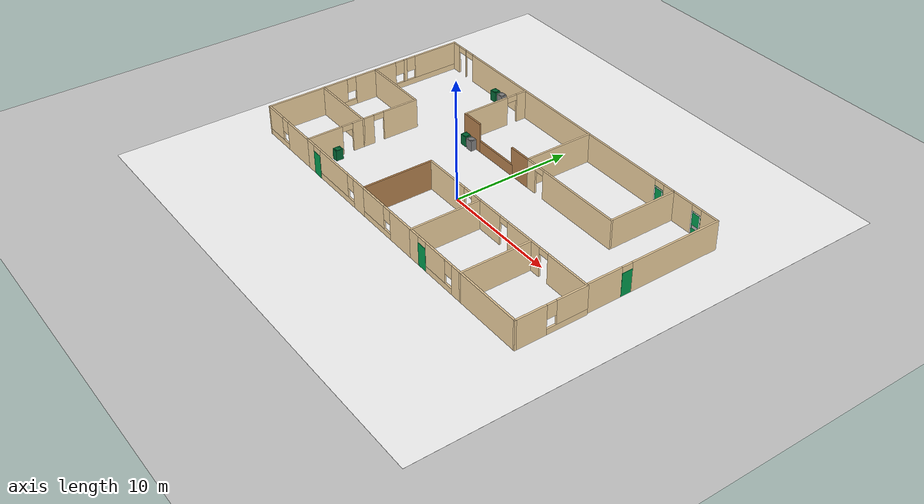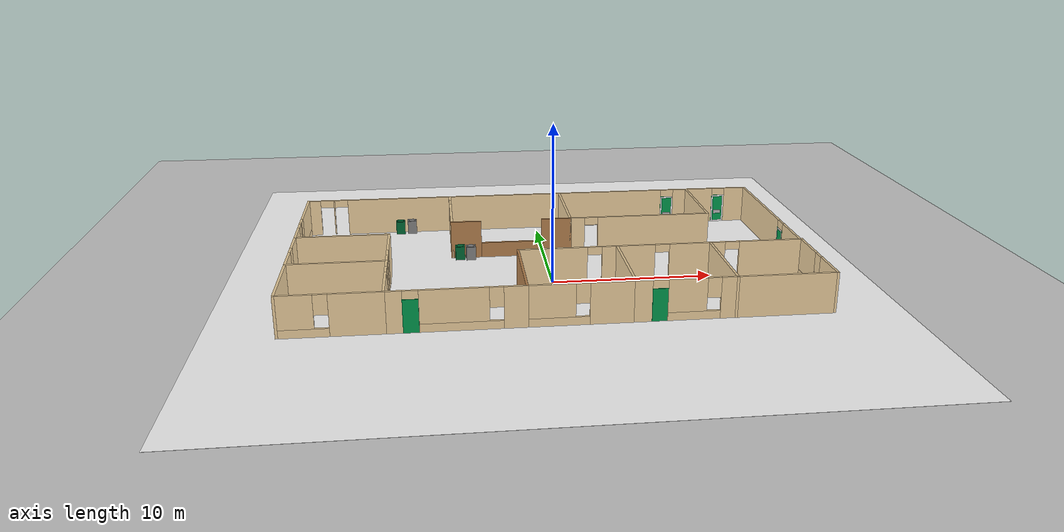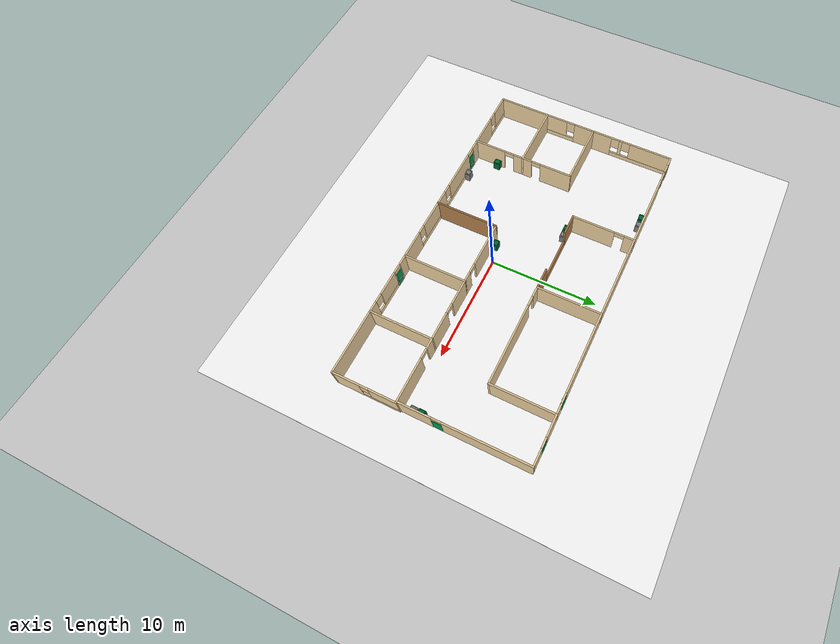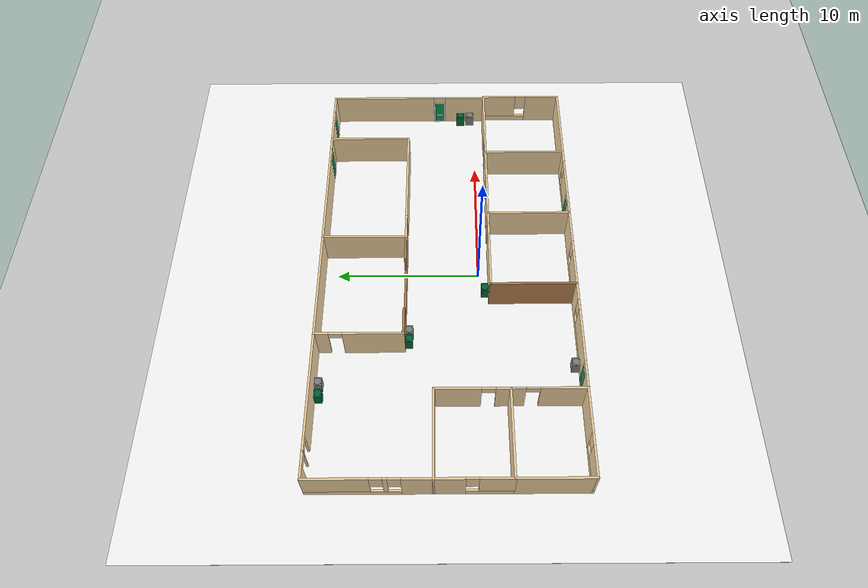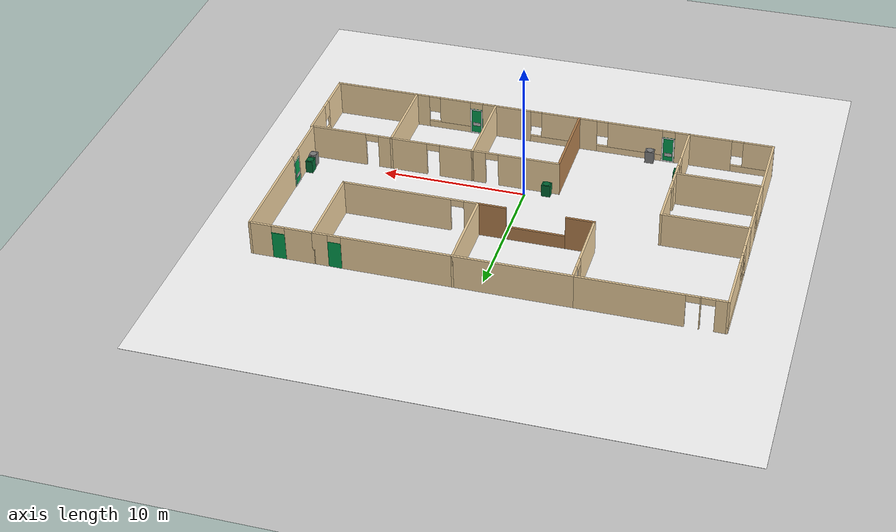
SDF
<sdf version="1.7">
 <world name="default">
  <plugin name="gazebo_ros_state" filename="libgazebo_ros_state.so"/>
  <light name="sun" type="directional">
   <pose>0 0 10 0 -0 0</pose>
   <diffuse>0.8 0.8 0.8 1</diffuse>
   <specular>0.2 0.2 0.2 1</specular>
   <attenuation>
    <range>1000</range>
    <constant>0.9</constant>
    <linear>0.01</linear>
    <quadratic>0.001</quadratic>
   </attenuation>
   <direction>-0.5 0.1 -0.9</direction>
   <spot><inner_angle>0</inner_angle><outer_angle>0</outer_angle><falloff>0</falloff></spot>
  </light>
  <model name="ground_plane">
   <static>1</static>
   <link name="link">
    <collision name="collision">
     <geometry><plane><normal>0 0 1</normal><size>100 100</size></plane></geometry>
     <surface><friction><ode><mu>100</mu><mu2>50</mu2></ode></friction></surface>
    </collision>
    <visual name="visual">
     <cast_shadows>0</cast_shadows>
     <geometry><plane><normal>0 0 1</normal><size>100 100</size></plane></geometry>
     <material>
      <script><uri>file://media/materials/scripts/gazebo.material</uri><name>Gazebo/Grey</name></script>
     </material>
    </visual>
   </link>
  </model>
  <gravity>0 0 -9.8</gravity>
  <magnetic_field>6e-06 2.3e-05 -4.2e-05</magnetic_field>
  <atmosphere type="adiabatic"/>
  <physics type="ode">
   <max_step_size>0.001</max_step_size>
   <real_time_factor>1</real_time_factor>
   <real_time_update_rate>1000</real_time_update_rate>
  </physics>
  <scene><ambient>0.4 0.4 0.4 1</ambient><background>0.7 0.7 0.7 1</background><shadows>1</shadows></scene>
  <audio><device>default</device></audio>
  <spherical_coordinates>
   <surface_model>EARTH_WGS84</surface_model>
   <latitude_deg>0</latitude_deg>
   <longitude_deg>0</longitude_deg>
   <elevation>0</elevation>
   <heading_deg>0</heading_deg>
  </spherical_coordinates>
  <model name="hospital_world">
   <pose>-0.19624 2.19188 0 0 -0 0</pose>
   <link name="Wall_100">
    <collision name="Wall_100_Collision">
     <geometry><box><size>2 0.15 2.5</size></box></geometry>
     <pose>0 0 1.25 0 -0 0</pose>
    </collision>
    <visual name="Wall_100_Visual">
     <pose>0 0 1.25 0 -0 0</pose>
     <geometry><box><size>2 0.15 2.5</size></box></geometry>
     <material>
      <script><uri>file://media/materials/scripts/gazebo.material</uri><name>Gazebo/Wood</name></script>
      <ambient>1 1 1 1</ambient>
     </material>
     <meta><layer>0</layer></meta>
    </visual>
    <pose>-4.97509 2.92511 0 0 -0 0</pose>
   </link>
   <link name="Wall_102">
    <collision name="Wall_102_Collision">
     <geometry><box><size>2 0.15 2.5</size></box></geometry>
     <pose>0 0 1.25 0 -0 0</pose>
    </collision>
    <visual name="Wall_102_Visual">
     <pose>0 0 1.25 0 -0 0</pose>
     <geometry><box><size>2 0.15 2.5</size></box></geometry>
     <material>
      <script><uri>file://media/materials/scripts/gazebo.material</uri><name>Gazebo/Wood</name></script>
      <ambient>1 1 1 1</ambient>
     </material>
     <meta><layer>0</layer></meta>
    </visual>
    <pose>1.02491 2.92511 0 0 -0 3.14159</pose>
   </link>
   <link name="Wall_104">
    <collision name="Wall_104_Collision">
     <geometry><box><size>4.3 0.15 1</size></box></geometry>
     <pose>0 0 0.5 0 -0 0</pose>
    </collision>
    <visual name="Wall_104_Visual">
     <pose>0 0 0.5 0 -0 0</pose>
     <geometry><box><size>4.3 0.15 1</size></box></geometry>
     <material>
      <script><uri>file://media/materials/scripts/gazebo.material</uri><name>Gazebo/Wood</name></script>
      <ambient>1 1 1 1</ambient>
     </material>
     <meta><layer>0</layer></meta>
    </visual>
    <pose>-1.97509 2.92511 0 0 -0 0</pose>
   </link>
   <link name="Wall_17">
    <collision name="Wall_17_Collision">
     <geometry><box><size>6 0.15 2.5</size></box></geometry>
     <pose>0 0 1.25 0 -0 0</pose>
    </collision>
    <visual name="Wall_17_Visual">
     <pose>0 0 1.25 0 -0 0</pose>
     <geometry><box><size>6 0.15 2.5</size></box></geometry>
     <material>
      <script><uri>file://media/materials/scripts/gazebo.material</uri><name>Gazebo/Grey</name></script>
      <ambient>0.921569 0.807843 0.615686 1</ambient>
     </material>
     <meta><layer>0</layer></meta>
    </visual>
    <pose>9.9 -5.85 0 0 -0 1.57076</pose>
   </link>
   <link name="Wall_21">
    <pose>6.975 -8.775 0 0 -0 -3.14155</pose>
    <visual name="Wall_21_Visual_0">
     <pose>-2.4903 0 1.25 0 -0 0</pose>
     <geometry><box><size>1.0194 0.15 2.5</size></box></geometry>
     <material>
      <script><uri>file://media/materials/scripts/gazebo.material</uri><name>Gazebo/Grey</name></script>
      <ambient>0.921569 0.807843 0.615686 1</ambient>
     </material>
     <meta><layer>0</layer></meta>
    </visual>
    <collision name="Wall_21_Collision_0">
     <geometry><box><size>1.0194 0.15 2.5</size></box></geometry>
     <pose>-2.4903 0 1.25 0 -0 0</pose>
    </collision>
    <visual name="Wall_21_Visual_1">
     <pose>2.48512 0 1.25 0 -0 0</pose>
     <geometry><box><size>1.02976 0.15 2.5</size></box></geometry>
     <material>
      <script><uri>file://media/materials/scripts/gazebo.material</uri><name>Gazebo/Grey</name></script>
      <ambient>0.921569 0.807843 0.615686 1</ambient>
     </material>
     <meta><layer>0</layer></meta>
    </visual>
    <collision name="Wall_21_Collision_1">
     <geometry><box><size>1.02976 0.15 2.5</size></box></geometry>
     <pose>2.48512 0 1.25 0 -0 0</pose>
    </collision>
    <visual name="Wall_21_Visual_2">
     <pose>-0.455184 0 0.25 0 -0 0</pose>
     <geometry><box><size>3.05084 0.15 0.5</size></box></geometry>
     <material>
      <script><uri>file://media/materials/scripts/gazebo.material</uri><name>Gazebo/Grey</name></script>
      <ambient>0.921569 0.807843 0.615686 1</ambient>
     </material>
     <meta><layer>0</layer></meta>
    </visual>
    <collision name="Wall_21_Collision_2">
     <geometry><box><size>3.05084 0.15 0.5</size></box></geometry>
     <pose>-0.455184 0 0.25 0 -0 0</pose>
    </collision>
    <visual name="Wall_21_Visual_3">
     <pose>-0.055184 0 1.5 0 -0 0</pose>
     <geometry><box><size>2.25084 0.15 2</size></box></geometry>
     <material>
      <script><uri>file://media/materials/scripts/gazebo.material</uri><name>Gazebo/Grey</name></script>
      <ambient>0.921569 0.807843 0.615686 1</ambient>
     </material>
     <meta><layer>0</layer></meta>
    </visual>
    <collision name="Wall_21_Collision_3">
     <geometry><box><size>2.25084 0.15 2</size></box></geometry>
     <pose>-0.055184 0 1.5 0 -0 0</pose>
    </collision>
    <visual name="Wall_21_Visual_4">
     <pose>-1.5806 0 1.9 0 -0 0</pose>
     <geometry><box><size>0.8 0.15 1.2</size></box></geometry>
     <material>
      <script><uri>file://media/materials/scripts/gazebo.material</uri><name>Gazebo/Grey</name></script>
      <ambient>0.921569 0.807843 0.615686 1</ambient>
     </material>
     <meta><layer>0</layer></meta>
    </visual>
    <collision name="Wall_21_Collision_4">
     <geometry><box><size>0.8 0.15 1.2</size></box></geometry>
     <pose>-1.5806 0 1.9 0 -0 0</pose>
    </collision>
    <visual name="Wall_21_Visual_5">
     <pose>1.52024 0 2.25 0 -0 0</pose>
     <geometry><box><size>0.9 0.15 0.5</size></box></geometry>
     <material>
      <script><uri>file://media/materials/scripts/gazebo.material</uri><name>Gazebo/Grey</name></script>
      <ambient>0.921569 0.807843 0.615686 1</ambient>
     </material>
     <meta><layer>0</layer></meta>
    </visual>
    <collision name="Wall_21_Collision_5">
     <geometry><box><size>0.9 0.15 0.5</size></box></geometry>
     <pose>1.52024 0 2.25 0 -0 0</pose>
    </collision>
   </link>
   <link name="Wall_22">
    <collision name="Wall_22_Collision">
     <geometry><box><size>6 0.15 2.5</size></box></geometry>
     <pose>0 0 1.25 0 -0 0</pose>
    </collision>
    <visual name="Wall_22_Visual">
     <pose>0 0 1.25 0 -0 0</pose>
     <geometry><box><size>6 0.15 2.5</size></box></geometry>
     <material>
      <script><uri>file://media/materials/scripts/gazebo.material</uri><name>Gazebo/Grey</name></script>
      <ambient>0.921569 0.807843 0.615686 1</ambient>
     </material>
     <meta><layer>0</layer></meta>
    </visual>
    <pose>4.05009 -5.85011 0 0 -0 1.5708</pose>
   </link>
   <link name="Wall_23">
    <pose>6.97509 -2.92511 0 0 -0 0</pose>
    <visual name="Wall_23_Visual_0">
     <pose>-1.77968 0 1.25 0 -0 0</pose>
     <geometry><box><size>2.44064 0.15 2.5</size></box></geometry>
     <material>
      <script><uri>file://media/materials/scripts/gazebo.material</uri><name>Gazebo/Grey</name></script>
      <ambient>0.921569 0.807843 0.615686 1</ambient>
     </material>
     <meta><layer>0</layer></meta>
    </visual>
    <collision name="Wall_23_Collision_0">
     <geometry><box><size>2.44064 0.15 2.5</size></box></geometry>
     <pose>-1.77968 0 1.25 0 -0 0</pose>
    </collision>
    <visual name="Wall_23_Visual_1">
     <pose>1.67032 0 1.25 0 -0 0</pose>
     <geometry><box><size>2.65936 0.15 2.5</size></box></geometry>
     <material>
      <script><uri>file://media/materials/scripts/gazebo.material</uri><name>Gazebo/Grey</name></script>
      <ambient>0.921569 0.807843 0.615686 1</ambient>
     </material>
     <meta><layer>0</layer></meta>
    </visual>
    <collision name="Wall_23_Collision_1">
     <geometry><box><size>2.65936 0.15 2.5</size></box></geometry>
     <pose>1.67032 0 1.25 0 -0 0</pose>
    </collision>
    <visual name="Wall_23_Visual_2">
     <pose>-0.10936 0 2.25 0 -0 0</pose>
     <geometry><box><size>0.9 0.15 0.5</size></box></geometry>
     <material>
      <script><uri>file://media/materials/scripts/gazebo.material</uri><name>Gazebo/Grey</name></script>
      <ambient>0.921569 0.807843 0.615686 1</ambient>
     </material>
     <meta><layer>0</layer></meta>
    </visual>
    <collision name="Wall_23_Collision_2">
     <geometry><box><size>0.9 0.15 0.5</size></box></geometry>
     <pose>-0.10936 0 2.25 0 -0 0</pose>
    </collision>
   </link>
   <link name="Wall_25">
    <pose>1.00009 -8.77511 0 0 -0 3.14159</pose>
    <visual name="Wall_25_Visual_0">
     <pose>-1.79812 0 1.25 0 -0 0</pose>
     <geometry><box><size>2.65377 0.15 2.5</size></box></geometry>
     <material>
      <script><uri>file://media/materials/scripts/gazebo.material</uri><name>Gazebo/Grey</name></script>
      <ambient>0.921569 0.807843 0.615686 1</ambient>
     </material>
     <meta><layer>0</layer></meta>
    </visual>
    <collision name="Wall_25_Collision_0">
     <geometry><box><size>2.65377 0.15 2.5</size></box></geometry>
     <pose>-1.79812 0 1.25 0 -0 0</pose>
    </collision>
    <visual name="Wall_25_Visual_1">
     <pose>1.32688 0 0.25 0 -0 0</pose>
     <geometry><box><size>3.59623 0.15 0.5</size></box></geometry>
     <material>
      <script><uri>file://media/materials/scripts/gazebo.material</uri><name>Gazebo/Grey</name></script>
      <ambient>0.921569 0.807843 0.615686 1</ambient>
     </material>
     <meta><layer>0</layer></meta>
    </visual>
    <collision name="Wall_25_Collision_1">
     <geometry><box><size>3.59623 0.15 0.5</size></box></geometry>
     <pose>1.32688 0 0.25 0 -0 0</pose>
    </collision>
    <visual name="Wall_25_Visual_2">
     <pose>1.72688 0 1.5 0 -0 0</pose>
     <geometry><box><size>2.79623 0.15 2</size></box></geometry>
     <material>
      <script><uri>file://media/materials/scripts/gazebo.material</uri><name>Gazebo/Grey</name></script>
      <ambient>0.921569 0.807843 0.615686 1</ambient>
     </material>
     <meta><layer>0</layer></meta>
    </visual>
    <collision name="Wall_25_Collision_2">
     <geometry><box><size>2.79623 0.15 2</size></box></geometry>
     <pose>1.72688 0 1.5 0 -0 0</pose>
    </collision>
    <visual name="Wall_25_Visual_3">
     <pose>-0.071231 0 1.9 0 -0 0</pose>
     <geometry><box><size>0.8 0.15 1.2</size></box></geometry>
     <material>
      <script><uri>file://media/materials/scripts/gazebo.material</uri><name>Gazebo/Grey</name></script>
      <ambient>0.921569 0.807843 0.615686 1</ambient>
     </material>
     <meta><layer>0</layer></meta>
    </visual>
    <collision name="Wall_25_Collision_3">
     <geometry><box><size>0.8 0.15 1.2</size></box></geometry>
     <pose>-0.071231 0 1.9 0 -0 0</pose>
    </collision>
   </link>
   <link name="Wall_26">
    <collision name="Wall_26_Collision">
     <geometry><box><size>6 0.15 2.5</size></box></geometry>
     <pose>0 0 1.25 0 -0 0</pose>
    </collision>
    <visual name="Wall_26_Visual">
     <pose>0 0 1.25 0 -0 0</pose>
     <geometry><box><size>6 0.15 2.5</size></box></geometry>
     <material>
      <script><uri>file://media/materials/scripts/gazebo.material</uri><name>Gazebo/Wood</name></script>
      <ambient>0.921569 0.807843 0.615686 1</ambient>
     </material>
     <meta><layer>0</layer></meta>
    </visual>
    <pose>-2.04991 -5.85011 0 0 -0 1.5708</pose>
   </link>
   <link name="Wall_27">
    <pose>1.00009 -2.92511 0 0 -0 0</pose>
    <visual name="Wall_27_Visual_0">
     <pose>-0.959565 0 1.25 0 -0 0</pose>
     <geometry><box><size>4.33087 0.15 2.5</size></box></geometry>
     <material>
      <script><uri>file://media/materials/scripts/gazebo.material</uri><name>Gazebo/Grey</name></script>
      <ambient>0.921569 0.807843 0.615686 1</ambient>
     </material>
     <meta><layer>0</layer></meta>
    </visual>
    <collision name="Wall_27_Collision_0">
     <geometry><box><size>4.33087 0.15 2.5</size></box></geometry>
     <pose>-0.959565 0 1.25 0 -0 0</pose>
    </collision>
    <visual name="Wall_27_Visual_1">
     <pose>2.61544 0 1.25 0 -0 0</pose>
     <geometry><box><size>1.01913 0.15 2.5</size></box></geometry>
     <material>
      <script><uri>file://media/materials/scripts/gazebo.material</uri><name>Gazebo/Grey</name></script>
      <ambient>0.921569 0.807843 0.615686 1</ambient>
     </material>
     <meta><layer>0</layer></meta>
    </visual>
    <collision name="Wall_27_Collision_1">
     <geometry><box><size>1.01913 0.15 2.5</size></box></geometry>
     <pose>2.61544 0 1.25 0 -0 0</pose>
    </collision>
    <visual name="Wall_27_Visual_2">
     <pose>1.65587 0 2.25 0 -0 0</pose>
     <geometry><box><size>0.9 0.15 0.5</size></box></geometry>
     <material>
      <script><uri>file://media/materials/scripts/gazebo.material</uri><name>Gazebo/Grey</name></script>
      <ambient>0.921569 0.807843 0.615686 1</ambient>
     </material>
     <meta><layer>0</layer></meta>
    </visual>
    <collision name="Wall_27_Collision_2">
     <geometry><box><size>0.9 0.15 0.5</size></box></geometry>
     <pose>1.65587 0 2.25 0 -0 0</pose>
    </collision>
   </link>
   <link name="Wall_39">
    <pose>-5.97491 -8.77511 0 0 -0 3.14159</pose>
    <visual name="Wall_39_Visual_0">
     <pose>-3.31601 0 1.25 0 -0 0</pose>
     <geometry><box><size>1.36798 0.15 2.5</size></box></geometry>
     <material>
      <script><uri>file://media/materials/scripts/gazebo.material</uri><name>Gazebo/Grey</name></script>
      <ambient>0.921569 0.807843 0.615686 1</ambient>
     </material>
     <meta><layer>0</layer></meta>
    </visual>
    <collision name="Wall_39_Collision_0">
     <geometry><box><size>1.36798 0.15 2.5</size></box></geometry>
     <pose>-3.31601 0 1.25 0 -0 0</pose>
    </collision>
    <visual name="Wall_39_Visual_1">
     <pose>3.47248 0 1.25 0 -0 0</pose>
     <geometry><box><size>1.05505 0.15 2.5</size></box></geometry>
     <material>
      <script><uri>file://media/materials/scripts/gazebo.material</uri><name>Gazebo/Grey</name></script>
      <ambient>0.921569 0.807843 0.615686 1</ambient>
     </material>
     <meta><layer>0</layer></meta>
    </visual>
    <collision name="Wall_39_Collision_1">
     <geometry><box><size>1.05505 0.15 2.5</size></box></geometry>
     <pose>3.47248 0 1.25 0 -0 0</pose>
    </collision>
    <visual name="Wall_39_Visual_2">
     <pose>-0.293532 0 0.25 0 -0 0</pose>
     <geometry><box><size>4.67697 0.15 0.5</size></box></geometry>
     <material>
      <script><uri>file://media/materials/scripts/gazebo.material</uri><name>Gazebo/Grey</name></script>
      <ambient>0.921569 0.807843 0.615686 1</ambient>
     </material>
     <meta><layer>0</layer></meta>
    </visual>
    <collision name="Wall_39_Collision_2">
     <geometry><box><size>4.67697 0.15 0.5</size></box></geometry>
     <pose>-0.293532 0 0.25 0 -0 0</pose>
    </collision>
    <visual name="Wall_39_Visual_3">
     <pose>0.106468 0 1.5 0 -0 0</pose>
     <geometry><box><size>3.87697 0.15 2</size></box></geometry>
     <material>
      <script><uri>file://media/materials/scripts/gazebo.material</uri><name>Gazebo/Grey</name></script>
      <ambient>0.921569 0.807843 0.615686 1</ambient>
     </material>
     <meta><layer>0</layer></meta>
    </visual>
    <collision name="Wall_39_Collision_3">
     <geometry><box><size>3.87697 0.15 2</size></box></geometry>
     <pose>0.106468 0 1.5 0 -0 0</pose>
    </collision>
    <visual name="Wall_39_Visual_4">
     <pose>-2.23202 0 1.9 0 -0 0</pose>
     <geometry><box><size>0.8 0.15 1.2</size></box></geometry>
     <material>
      <script><uri>file://media/materials/scripts/gazebo.material</uri><name>Gazebo/Grey</name></script>
      <ambient>0.921569 0.807843 0.615686 1</ambient>
     </material>
     <meta><layer>0</layer></meta>
    </visual>
    <collision name="Wall_39_Collision_4">
     <geometry><box><size>0.8 0.15 1.2</size></box></geometry>
     <pose>-2.23202 0 1.9 0 -0 0</pose>
    </collision>
    <visual name="Wall_39_Visual_5">
     <pose>2.49495 0 2.25 0 -0 0</pose>
     <geometry><box><size>0.9 0.15 0.5</size></box></geometry>
     <material>
      <script><uri>file://media/materials/scripts/gazebo.material</uri><name>Gazebo/Grey</name></script>
      <ambient>0.921569 0.807843 0.615686 1</ambient>
     </material>
     <meta><layer>0</layer></meta>
    </visual>
    <collision name="Wall_39_Collision_5">
     <geometry><box><size>0.9 0.15 0.5</size></box></geometry>
     <pose>2.49495 0 2.25 0 -0 0</pose>
    </collision>
   </link>
   <link name="Wall_40">
    <pose>-12.8249 -8.77511 0 0 -0 3.14159</pose>
    <visual name="Wall_40_Visual_0">
     <pose>-1.46725 0 1.25 0 -0 0</pose>
     <geometry><box><size>3.0655 0.15 2.5</size></box></geometry>
     <material>
      <script><uri>file://media/materials/scripts/gazebo.material</uri><name>Gazebo/Grey</name></script>
      <ambient>0.921569 0.807843 0.615686 1</ambient>
     </material>
     <meta><layer>0</layer></meta>
    </visual>
    <collision name="Wall_40_Collision_0">
     <geometry><box><size>3.0655 0.15 2.5</size></box></geometry>
     <pose>-1.46725 0 1.25 0 -0 0</pose>
    </collision>
    <visual name="Wall_40_Visual_1">
     <pose>1.53275 0 0.25 0 -0 0</pose>
     <geometry><box><size>2.9345 0.15 0.5</size></box></geometry>
     <material>
      <script><uri>file://media/materials/scripts/gazebo.material</uri><name>Gazebo/Grey</name></script>
      <ambient>0.921569 0.807843 0.615686 1</ambient>
     </material>
     <meta><layer>0</layer></meta>
    </visual>
    <collision name="Wall_40_Collision_1">
     <geometry><box><size>2.9345 0.15 0.5</size></box></geometry>
     <pose>1.53275 0 0.25 0 -0 0</pose>
    </collision>
    <visual name="Wall_40_Visual_2">
     <pose>1.93275 0 1.5 0 -0 0</pose>
     <geometry><box><size>2.1345 0.15 2</size></box></geometry>
     <material>
      <script><uri>file://media/materials/scripts/gazebo.material</uri><name>Gazebo/Grey</name></script>
      <ambient>0.921569 0.807843 0.615686 1</ambient>
     </material>
     <meta><layer>0</layer></meta>
    </visual>
    <collision name="Wall_40_Collision_2">
     <geometry><box><size>2.1345 0.15 2</size></box></geometry>
     <pose>1.93275 0 1.5 0 -0 0</pose>
    </collision>
    <visual name="Wall_40_Visual_3">
     <pose>0.465498 0 1.9 0 -0 0</pose>
     <geometry><box><size>0.8 0.15 1.2</size></box></geometry>
     <material>
      <script><uri>file://media/materials/scripts/gazebo.material</uri><name>Gazebo/Grey</name></script>
      <ambient>0.921569 0.807843 0.615686 1</ambient>
     </material>
     <meta><layer>0</layer></meta>
    </visual>
    <collision name="Wall_40_Collision_3">
     <geometry><box><size>0.8 0.15 1.2</size></box></geometry>
     <pose>0.465498 0 1.9 0 -0 0</pose>
    </collision>
   </link>
   <link name="Wall_41">
    <collision name="Wall_41_Collision">
     <geometry><box><size>5 0.15 2.5</size></box></geometry>
     <pose>0 0 1.25 0 -0 0</pose>
    </collision>
    <visual name="Wall_41_Visual">
     <pose>0 0 1.25 0 -0 0</pose>
     <geometry><box><size>5 0.15 2.5</size></box></geometry>
     <material>
      <script><uri>file://media/materials/scripts/gazebo.material</uri><name>Gazebo/Grey</name></script>
      <ambient>0.921569 0.807843 0.615686 1</ambient>
     </material>
     <meta><layer>0</layer></meta>
    </visual>
    <pose>-15.7499 -6.35011 0 0 -0 1.5708</pose>
   </link>
   <link name="Wall_42">
    <collision name="Wall_42_Collision">
     <geometry><box><size>6 0.15 2.5</size></box></geometry>
     <pose>0 0 1.25 0 -0 0</pose>
    </collision>
    <visual name="Wall_42_Visual">
     <pose>0 0 1.25 0 -0 0</pose>
     <geometry><box><size>6 0.15 2.5</size></box></geometry>
     <material>
      <script><uri>file://media/materials/scripts/gazebo.material</uri><name>Gazebo/Grey</name></script>
      <ambient>0.921569 0.807843 0.615686 1</ambient>
     </material>
     <meta><layer>0</layer></meta>
    </visual>
    <pose>-12.8249 -3.92511 0 0 -0 0</pose>
   </link>
   <link name="Wall_43">
    <pose>-9.89991 -1.50011 0 0 -0 1.5708</pose>
    <visual name="Wall_43_Visual_0">
     <pose>-1.99454 0 1.25 0 -0 0</pose>
     <geometry><box><size>1.01092 0.15 2.5</size></box></geometry>
     <material>
      <script><uri>file://media/materials/scripts/gazebo.material</uri><name>Gazebo/Grey</name></script>
      <ambient>0.921569 0.807843 0.615686 1</ambient>
     </material>
     <meta><layer>0</layer></meta>
    </visual>
    <collision name="Wall_43_Collision_0">
     <geometry><box><size>1.01092 0.15 2.5</size></box></geometry>
     <pose>-1.99454 0 1.25 0 -0 0</pose>
    </collision>
    <visual name="Wall_43_Visual_1">
     <pose>0.955458 0 1.25 0 -0 0</pose>
     <geometry><box><size>3.08908 0.15 2.5</size></box></geometry>
     <material>
      <script><uri>file://media/materials/scripts/gazebo.material</uri><name>Gazebo/Grey</name></script>
      <ambient>0.921569 0.807843 0.615686 1</ambient>
     </material>
     <meta><layer>0</layer></meta>
    </visual>
    <collision name="Wall_43_Collision_1">
     <geometry><box><size>3.08908 0.15 2.5</size></box></geometry>
     <pose>0.955458 0 1.25 0 -0 0</pose>
    </collision>
    <visual name="Wall_43_Visual_2">
     <pose>-1.03908 0 2.25 0 -0 0</pose>
     <geometry><box><size>0.9 0.15 0.5</size></box></geometry>
     <material>
      <script><uri>file://media/materials/scripts/gazebo.material</uri><name>Gazebo/Grey</name></script>
      <ambient>0.921569 0.807843 0.615686 1</ambient>
     </material>
     <meta><layer>0</layer></meta>
    </visual>
    <collision name="Wall_43_Collision_2">
     <geometry><box><size>0.9 0.15 0.5</size></box></geometry>
     <pose>-1.03908 0 2.25 0 -0 0</pose>
    </collision>
   </link>
   <link name="Wall_44">
    <collision name="Wall_44_Collision">
     <geometry><box><size>6 0.15 2.5</size></box></geometry>
     <pose>0 0 1.25 0 -0 0</pose>
    </collision>
    <visual name="Wall_44_Visual">
     <pose>0 0 1.25 0 -0 0</pose>
     <geometry><box><size>6 0.15 2.5</size></box></geometry>
     <material>
      <script><uri>file://media/materials/scripts/gazebo.material</uri><name>Gazebo/Grey</name></script>
      <ambient>0.921569 0.807843 0.615686 1</ambient>
     </material>
     <meta><layer>0</layer></meta>
    </visual>
    <pose>-12.825 0.925001 0 0 -0 3.14155</pose>
   </link>
   <link name="Wall_45">
    <pose>-15.75 -1.5 0 0 -0 -1.57076</pose>
    <visual name="Wall_45_Visual_0">
     <pose>-1.49533 0 1.25 0 -0 0</pose>
     <geometry><box><size>2.00935 0.15 2.5</size></box></geometry>
     <material>
      <script><uri>file://media/materials/scripts/gazebo.material</uri><name>Gazebo/Grey</name></script>
      <ambient>0.921569 0.807843 0.615686 1</ambient>
     </material>
     <meta><layer>0</layer></meta>
    </visual>
    <collision name="Wall_45_Collision_0">
     <geometry><box><size>2.00935 0.15 2.5</size></box></geometry>
     <pose>-1.49533 0 1.25 0 -0 0</pose>
    </collision>
    <visual name="Wall_45_Visual_1">
     <pose>1.00467 0 0.25 0 -0 0</pose>
     <geometry><box><size>2.99065 0.15 0.5</size></box></geometry>
     <material>
      <script><uri>file://media/materials/scripts/gazebo.material</uri><name>Gazebo/Grey</name></script>
      <ambient>0.921569 0.807843 0.615686 1</ambient>
     </material>
     <meta><layer>0</layer></meta>
    </visual>
    <collision name="Wall_45_Collision_1">
     <geometry><box><size>2.99065 0.15 0.5</size></box></geometry>
     <pose>1.00467 0 0.25 0 -0 0</pose>
    </collision>
    <visual name="Wall_45_Visual_2">
     <pose>1.40467 0 1.5 0 -0 0</pose>
     <geometry><box><size>2.19065 0.15 2</size></box></geometry>
     <material>
      <script><uri>file://media/materials/scripts/gazebo.material</uri><name>Gazebo/Grey</name></script>
      <ambient>0.921569 0.807843 0.615686 1</ambient>
     </material>
     <meta><layer>0</layer></meta>
    </visual>
    <collision name="Wall_45_Collision_2">
     <geometry><box><size>2.19065 0.15 2</size></box></geometry>
     <pose>1.40467 0 1.5 0 -0 0</pose>
    </collision>
    <visual name="Wall_45_Visual_3">
     <pose>-0.090652 0 1.9 0 -0 0</pose>
     <geometry><box><size>0.8 0.15 1.2</size></box></geometry>
     <material>
      <script><uri>file://media/materials/scripts/gazebo.material</uri><name>Gazebo/Grey</name></script>
      <ambient>0.921569 0.807843 0.615686 1</ambient>
     </material>
     <meta><layer>0</layer></meta>
    </visual>
    <collision name="Wall_45_Collision_3">
     <geometry><box><size>0.8 0.15 1.2</size></box></geometry>
     <pose>-0.090652 0 1.9 0 -0 0</pose>
    </collision>
   </link>
   <link name="Wall_47">
    <pose>-9.89991 -6.35011 0 0 -0 -1.5708</pose>
    <visual name="Wall_47_Visual_0">
     <pose>-1.98106 0 1.25 0 -0 0</pose>
     <geometry><box><size>1.03789 0.15 2.5</size></box></geometry>
     <material>
      <script><uri>file://media/materials/scripts/gazebo.material</uri><name>Gazebo/Grey</name></script>
      <ambient>0.921569 0.807843 0.615686 1</ambient>
     </material>
     <meta><layer>0</layer></meta>
    </visual>
    <collision name="Wall_47_Collision_0">
     <geometry><box><size>1.03789 0.15 2.5</size></box></geometry>
     <pose>-1.98106 0 1.25 0 -0 0</pose>
    </collision>
    <visual name="Wall_47_Visual_1">
     <pose>0.968943 0 1.25 0 -0 0</pose>
     <geometry><box><size>3.06211 0.15 2.5</size></box></geometry>
     <material>
      <script><uri>file://media/materials/scripts/gazebo.material</uri><name>Gazebo/Grey</name></script>
      <ambient>0.921569 0.807843 0.615686 1</ambient>
     </material>
     <meta><layer>0</layer></meta>
    </visual>
    <collision name="Wall_47_Collision_1">
     <geometry><box><size>3.06211 0.15 2.5</size></box></geometry>
     <pose>0.968943 0 1.25 0 -0 0</pose>
    </collision>
    <visual name="Wall_47_Visual_2">
     <pose>-1.01211 0 2.25 0 -0 0</pose>
     <geometry><box><size>0.9 0.15 0.5</size></box></geometry>
     <material>
      <script><uri>file://media/materials/scripts/gazebo.material</uri><name>Gazebo/Grey</name></script>
      <ambient>0.921569 0.807843 0.615686 1</ambient>
     </material>
     <meta><layer>0</layer></meta>
    </visual>
    <collision name="Wall_47_Collision_2">
     <geometry><box><size>0.9 0.15 0.5</size></box></geometry>
     <pose>-1.01211 0 2.25 0 -0 0</pose>
    </collision>
   </link>
   <link name="Wall_49">
    <pose>-15.7501 4.85011 0 0 -0 1.5708</pose>
    <visual name="Wall_49_Visual_0">
     <pose>-3.00353 0 1.25 0 -0 0</pose>
     <geometry><box><size>1.99293 0.15 2.5</size></box></geometry>
     <material>
      <script><uri>file://media/materials/scripts/gazebo.material</uri><name>Gazebo/Grey</name></script>
      <ambient>0.921569 0.807843 0.615686 1</ambient>
     </material>
     <meta><layer>0</layer></meta>
    </visual>
    <collision name="Wall_49_Collision_0">
     <geometry><box><size>1.99293 0.15 2.5</size></box></geometry>
     <pose>-3.00353 0 1.25 0 -0 0</pose>
    </collision>
    <visual name="Wall_49_Visual_1">
     <pose>0.996466 0 0.25 0 -0 0</pose>
     <geometry><box><size>6.00707 0.15 0.5</size></box></geometry>
     <material>
      <script><uri>file://media/materials/scripts/gazebo.material</uri><name>Gazebo/Grey</name></script>
      <ambient>0.921569 0.807843 0.615686 1</ambient>
     </material>
     <meta><layer>0</layer></meta>
    </visual>
    <collision name="Wall_49_Collision_1">
     <geometry><box><size>6.00707 0.15 0.5</size></box></geometry>
     <pose>0.996466 0 0.25 0 -0 0</pose>
    </collision>
    <visual name="Wall_49_Visual_2">
     <pose>-1.06092 0 1.5 0 -0 0</pose>
     <geometry><box><size>0.2923 0.15 2</size></box></geometry>
     <material>
      <script><uri>file://media/materials/scripts/gazebo.material</uri><name>Gazebo/Grey</name></script>
      <ambient>0.921569 0.807843 0.615686 1</ambient>
     </material>
     <meta><layer>0</layer></meta>
    </visual>
    <collision name="Wall_49_Collision_2">
     <geometry><box><size>0.2923 0.15 2</size></box></geometry>
     <pose>-1.06092 0 1.5 0 -0 0</pose>
    </collision>
    <visual name="Wall_49_Visual_3">
     <pose>1.94262 0 1.5 0 -0 0</pose>
     <geometry><box><size>4.11477 0.15 2</size></box></geometry>
     <material>
      <script><uri>file://media/materials/scripts/gazebo.material</uri><name>Gazebo/Grey</name></script>
      <ambient>0.921569 0.807843 0.615686 1</ambient>
     </material>
     <meta><layer>0</layer></meta>
    </visual>
    <collision name="Wall_49_Collision_3">
     <geometry><box><size>4.11477 0.15 2</size></box></geometry>
     <pose>1.94262 0 1.5 0 -0 0</pose>
    </collision>
    <visual name="Wall_49_Visual_4">
     <pose>-1.60707 0 1.9 0 -0 0</pose>
     <geometry><box><size>0.8 0.15 1.2</size></box></geometry>
     <material>
      <script><uri>file://media/materials/scripts/gazebo.material</uri><name>Gazebo/Grey</name></script>
      <ambient>0.921569 0.807843 0.615686 1</ambient>
     </material>
     <meta><layer>0</layer></meta>
    </visual>
    <collision name="Wall_49_Collision_4">
     <geometry><box><size>0.8 0.15 1.2</size></box></geometry>
     <pose>-1.60707 0 1.9 0 -0 0</pose>
    </collision>
    <visual name="Wall_49_Visual_5">
     <pose>-0.514768 0 1.9 0 -0 0</pose>
     <geometry><box><size>0.8 0.15 1.2</size></box></geometry>
     <material>
      <script><uri>file://media/materials/scripts/gazebo.material</uri><name>Gazebo/Grey</name></script>
      <ambient>0.921569 0.807843 0.615686 1</ambient>
     </material>
     <meta><layer>0</layer></meta>
    </visual>
    <collision name="Wall_49_Collision_5">
     <geometry><box><size>0.8 0.15 1.2</size></box></geometry>
     <pose>-0.514768 0 1.9 0 -0 0</pose>
    </collision>
   </link>
   <link name="Wall_51">
    <pose>-10.8251 8.77511 0 0 -0 0</pose>
    <visual name="Wall_51_Visual_0">
     <pose>-4.55288 0 1.25 0 -0 0</pose>
     <geometry><box><size>0.894234 0.15 2.5</size></box></geometry>
     <material>
      <script><uri>file://media/materials/scripts/gazebo.material</uri><name>Gazebo/Grey</name></script>
      <ambient>0.921569 0.807843 0.615686 1</ambient>
     </material>
     <meta><layer>0</layer></meta>
    </visual>
    <collision name="Wall_51_Collision_0">
     <geometry><box><size>0.894234 0.15 2.5</size></box></geometry>
     <pose>-4.55288 0 1.25 0 -0 0</pose>
    </collision>
    <visual name="Wall_51_Visual_1">
     <pose>-3.1703 0 1.25 0 -0 0</pose>
     <geometry><box><size>0.070934 0.15 2.5</size></box></geometry>
     <material>
      <script><uri>file://media/materials/scripts/gazebo.material</uri><name>Gazebo/Grey</name></script>
      <ambient>0.921569 0.807843 0.615686 1</ambient>
     </material>
     <meta><layer>0</layer></meta>
    </visual>
    <collision name="Wall_51_Collision_1">
     <geometry><box><size>0.070934 0.15 2.5</size></box></geometry>
     <pose>-3.1703 0 1.25 0 -0 0</pose>
    </collision>
    <visual name="Wall_51_Visual_2">
     <pose>1.38258 0 1.25 0 -0 0</pose>
     <geometry><box><size>7.23483 0.15 2.5</size></box></geometry>
     <material>
      <script><uri>file://media/materials/scripts/gazebo.material</uri><name>Gazebo/Grey</name></script>
      <ambient>0.921569 0.807843 0.615686 1</ambient>
     </material>
     <meta><layer>0</layer></meta>
    </visual>
    <collision name="Wall_51_Collision_2">
     <geometry><box><size>7.23483 0.15 2.5</size></box></geometry>
     <pose>1.38258 0 1.25 0 -0 0</pose>
    </collision>
    <visual name="Wall_51_Visual_3">
     <pose>-3.65577 0 2.25 0 -0 0</pose>
     <geometry><box><size>0.9 0.15 0.5</size></box></geometry>
     <material>
      <script><uri>file://media/materials/scripts/gazebo.material</uri><name>Gazebo/Grey</name></script>
      <ambient>0.921569 0.807843 0.615686 1</ambient>
     </material>
     <meta><layer>0</layer></meta>
    </visual>
    <collision name="Wall_51_Collision_3">
     <geometry><box><size>0.9 0.15 0.5</size></box></geometry>
     <pose>-3.65577 0 2.25 0 -0 0</pose>
    </collision>
    <visual name="Wall_51_Visual_4">
     <pose>-2.68483 0 2.25 0 -0 0</pose>
     <geometry><box><size>0.9 0.15 0.5</size></box></geometry>
     <material>
      <script><uri>file://media/materials/scripts/gazebo.material</uri><name>Gazebo/Grey</name></script>
      <ambient>0.921569 0.807843 0.615686 1</ambient>
     </material>
     <meta><layer>0</layer></meta>
    </visual>
    <collision name="Wall_51_Collision_4">
     <geometry><box><size>0.9 0.15 0.5</size></box></geometry>
     <pose>-2.68483 0 2.25 0 -0 0</pose>
    </collision>
   </link>
   <link name="Wall_53">
    <pose>-5.90009 5.85011 0 0 -0 -1.5708</pose>
    <visual name="Wall_53_Visual_0">
     <pose>-2.48944 0 1.25 0 -0 0</pose>
     <geometry><box><size>1.02112 0.15 2.5</size></box></geometry>
     <material>
      <script><uri>file://media/materials/scripts/gazebo.material</uri><name>Gazebo/Grey</name></script>
      <ambient>0.921569 0.807843 0.615686 1</ambient>
     </material>
     <meta><layer>0</layer></meta>
    </visual>
    <collision name="Wall_53_Collision_0">
     <geometry><box><size>1.02112 0.15 2.5</size></box></geometry>
     <pose>-2.48944 0 1.25 0 -0 0</pose>
    </collision>
    <visual name="Wall_53_Visual_1">
     <pose>0.960559 0 1.25 0 -0 0</pose>
     <geometry><box><size>4.07888 0.15 2.5</size></box></geometry>
     <material>
      <script><uri>file://media/materials/scripts/gazebo.material</uri><name>Gazebo/Grey</name></script>
      <ambient>0.921569 0.807843 0.615686 1</ambient>
     </material>
     <meta><layer>0</layer></meta>
    </visual>
    <collision name="Wall_53_Collision_1">
     <geometry><box><size>4.07888 0.15 2.5</size></box></geometry>
     <pose>0.960559 0 1.25 0 -0 0</pose>
    </collision>
    <visual name="Wall_53_Visual_2">
     <pose>-1.52888 0 2.25 0 -0 0</pose>
     <geometry><box><size>0.9 0.15 0.5</size></box></geometry>
     <material>
      <script><uri>file://media/materials/scripts/gazebo.material</uri><name>Gazebo/Grey</name></script>
      <ambient>0.921569 0.807843 0.615686 1</ambient>
     </material>
     <meta><layer>0</layer></meta>
    </visual>
    <collision name="Wall_53_Collision_2">
     <geometry><box><size>0.9 0.15 0.5</size></box></geometry>
     <pose>-1.52888 0 2.25 0 -0 0</pose>
    </collision>
   </link>
   <link name="Wall_55">
    <collision name="Wall_55_Collision">
     <geometry><box><size>6 0.15 2.5</size></box></geometry>
     <pose>0 0 1.25 0 -0 0</pose>
    </collision>
    <visual name="Wall_55_Visual">
     <pose>0 0 1.25 0 -0 0</pose>
     <geometry><box><size>6 0.15 2.5</size></box></geometry>
     <material>
      <script><uri>file://media/materials/scripts/gazebo.material</uri><name>Gazebo/Grey</name></script>
      <ambient>0.921569 0.807843 0.615686 1</ambient>
     </material>
     <meta><layer>0</layer></meta>
    </visual>
    <pose>1.94991 5.85011 0 0 -0 1.5708</pose>
   </link>
   <link name="Wall_56">
    <collision name="Wall_56_Collision">
     <geometry><box><size>8 0.15 2.5</size></box></geometry>
     <pose>0 0 1.25 0 -0 0</pose>
    </collision>
    <visual name="Wall_56_Visual">
     <pose>0 0 1.25 0 -0 0</pose>
     <geometry><box><size>8 0.15 2.5</size></box></geometry>
     <material>
      <script><uri>file://media/materials/scripts/gazebo.material</uri><name>Gazebo/Grey</name></script>
      <ambient>0.921569 0.807843 0.615686 1</ambient>
     </material>
     <meta><layer>0</layer></meta>
    </visual>
    <pose>-1.97509 8.77511 0 0 -0 3.14159</pose>
   </link>
   <link name="Wall_58">
    <pose>6.62491 8.77511 0 0 -0 0</pose>
    <visual name="Wall_58_Visual_0">
     <pose>-0.982488 0 1.25 0 -0 0</pose>
     <geometry><box><size>7.53503 0.15 2.5</size></box></geometry>
     <material>
      <script><uri>file://media/materials/scripts/gazebo.material</uri><name>Gazebo/Grey</name></script>
      <ambient>0.921569 0.807843 0.615686 1</ambient>
     </material>
     <meta><layer>0</layer></meta>
    </visual>
    <collision name="Wall_58_Collision_0">
     <geometry><box><size>7.53503 0.15 2.5</size></box></geometry>
     <pose>-0.982488 0 1.25 0 -0 0</pose>
    </collision>
    <visual name="Wall_58_Visual_1">
     <pose>4.21751 0 1.25 0 -0 0</pose>
     <geometry><box><size>1.06498 0.15 2.5</size></box></geometry>
     <material>
      <script><uri>file://media/materials/scripts/gazebo.material</uri><name>Gazebo/Grey</name></script>
      <ambient>0.921569 0.807843 0.615686 1</ambient>
     </material>
     <meta><layer>0</layer></meta>
    </visual>
    <collision name="Wall_58_Collision_1">
     <geometry><box><size>1.06498 0.15 2.5</size></box></geometry>
     <pose>4.21751 0 1.25 0 -0 0</pose>
    </collision>
    <visual name="Wall_58_Visual_2">
     <pose>3.23502 0 2.25 0 -0 0</pose>
     <geometry><box><size>0.9 0.15 0.5</size></box></geometry>
     <material>
      <script><uri>file://media/materials/scripts/gazebo.material</uri><name>Gazebo/Grey</name></script>
      <ambient>0.921569 0.807843 0.615686 1</ambient>
     </material>
     <meta><layer>0</layer></meta>
    </visual>
    <collision name="Wall_58_Collision_2">
     <geometry><box><size>0.9 0.15 0.5</size></box></geometry>
     <pose>3.23502 0 2.25 0 -0 0</pose>
    </collision>
   </link>
   <link name="Wall_59">
    <collision name="Wall_59_Collision">
     <geometry><box><size>6 0.15 2.5</size></box></geometry>
     <pose>0 0 1.25 0 -0 0</pose>
    </collision>
    <visual name="Wall_59_Visual">
     <pose>0 0 1.25 0 -0 0</pose>
     <geometry><box><size>6 0.15 2.5</size></box></geometry>
     <material>
      <script><uri>file://media/materials/scripts/gazebo.material</uri><name>Gazebo/Grey</name></script>
      <ambient>0.921569 0.807843 0.615686 1</ambient>
     </material>
     <meta><layer>0</layer></meta>
    </visual>
    <pose>11.2999 5.85011 0 0 -0 -1.5708</pose>
   </link>
   <link name="Wall_60">
    <pose>6.62491 2.92511 0 0 -0 3.14159</pose>
    <visual name="Wall_60_Visual_0">
     <pose>-0.968894 0 1.25 0 -0 0</pose>
     <geometry><box><size>7.56221 0.15 2.5</size></box></geometry>
     <material>
      <script><uri>file://media/materials/scripts/gazebo.material</uri><name>Gazebo/Grey</name></script>
      <ambient>0.921569 0.807843 0.615686 1</ambient>
     </material>
     <meta><layer>0</layer></meta>
    </visual>
    <collision name="Wall_60_Collision_0">
     <geometry><box><size>7.56221 0.15 2.5</size></box></geometry>
     <pose>-0.968894 0 1.25 0 -0 0</pose>
    </collision>
    <visual name="Wall_60_Visual_1">
     <pose>4.23111 0 1.25 0 -0 0</pose>
     <geometry><box><size>1.03779 0.15 2.5</size></box></geometry>
     <material>
      <script><uri>file://media/materials/scripts/gazebo.material</uri><name>Gazebo/Grey</name></script>
      <ambient>0.921569 0.807843 0.615686 1</ambient>
     </material>
     <meta><layer>0</layer></meta>
    </visual>
    <collision name="Wall_60_Collision_1">
     <geometry><box><size>1.03779 0.15 2.5</size></box></geometry>
     <pose>4.23111 0 1.25 0 -0 0</pose>
    </collision>
    <visual name="Wall_60_Visual_2">
     <pose>3.26221 0 2.25 0 -0 0</pose>
     <geometry><box><size>0.9 0.15 0.5</size></box></geometry>
     <material>
      <script><uri>file://media/materials/scripts/gazebo.material</uri><name>Gazebo/Grey</name></script>
      <ambient>0.921569 0.807843 0.615686 1</ambient>
     </material>
     <meta><layer>0</layer></meta>
    </visual>
    <collision name="Wall_60_Collision_2">
     <geometry><box><size>0.9 0.15 0.5</size></box></geometry>
     <pose>3.26221 0 2.25 0 -0 0</pose>
    </collision>
   </link>
   <link name="Wall_83">
    <pose>13.4749 8.77511 0 0 -0 0</pose>
    <visual name="Wall_83_Visual_0">
     <pose>-1.24216 0 1.25 0 -0 0</pose>
     <geometry><box><size>2.01568 0.15 2.5</size></box></geometry>
     <material>
      <script><uri>file://media/materials/scripts/gazebo.material</uri><name>Gazebo/Grey</name></script>
      <ambient>0.921569 0.807843 0.615686 1</ambient>
     </material>
     <meta><layer>0</layer></meta>
    </visual>
    <collision name="Wall_83_Collision_0">
     <geometry><box><size>2.01568 0.15 2.5</size></box></geometry>
     <pose>-1.24216 0 1.25 0 -0 0</pose>
    </collision>
    <visual name="Wall_83_Visual_1">
     <pose>1.45784 0 1.25 0 -0 0</pose>
     <geometry><box><size>1.58432 0.15 2.5</size></box></geometry>
     <material>
      <script><uri>file://media/materials/scripts/gazebo.material</uri><name>Gazebo/Grey</name></script>
      <ambient>0.921569 0.807843 0.615686 1</ambient>
     </material>
     <meta><layer>0</layer></meta>
    </visual>
    <collision name="Wall_83_Collision_1">
     <geometry><box><size>1.58432 0.15 2.5</size></box></geometry>
     <pose>1.45784 0 1.25 0 -0 0</pose>
    </collision>
    <visual name="Wall_83_Visual_2">
     <pose>0.21568 0 2.25 0 -0 0</pose>
     <geometry><box><size>0.9 0.15 0.5</size></box></geometry>
     <material>
      <script><uri>file://media/materials/scripts/gazebo.material</uri><name>Gazebo/Grey</name></script>
      <ambient>0.921569 0.807843 0.615686 1</ambient>
     </material>
     <meta><layer>0</layer></meta>
    </visual>
    <collision name="Wall_83_Collision_2">
     <geometry><box><size>0.9 0.15 0.5</size></box></geometry>
     <pose>0.21568 0 2.25 0 -0 0</pose>
    </collision>
   </link>
   <link name="Wall_88">
    <pose>15.6499 2.97512 0 0 -0 -1.5708</pose>
    <visual name="Wall_88_Visual_0">
     <pose>-1.95097 0 1.25 0 -0 0</pose>
     <geometry><box><size>7.84806 0.15 2.5</size></box></geometry>
     <material>
      <script><uri>file://media/materials/scripts/gazebo.material</uri><name>Gazebo/Grey</name></script>
      <ambient>0.921569 0.807843 0.615686 1</ambient>
     </material>
     <meta><layer>0</layer></meta>
    </visual>
    <collision name="Wall_88_Collision_0">
     <geometry><box><size>7.84806 0.15 2.5</size></box></geometry>
     <pose>-1.95097 0 1.25 0 -0 0</pose>
    </collision>
    <visual name="Wall_88_Visual_1">
     <pose>4.37403 0 1.25 0 -0 0</pose>
     <geometry><box><size>3.00194 0.15 2.5</size></box></geometry>
     <material>
      <script><uri>file://media/materials/scripts/gazebo.material</uri><name>Gazebo/Grey</name></script>
      <ambient>0.921569 0.807843 0.615686 1</ambient>
     </material>
     <meta><layer>0</layer></meta>
    </visual>
    <collision name="Wall_88_Collision_1">
     <geometry><box><size>3.00194 0.15 2.5</size></box></geometry>
     <pose>4.37403 0 1.25 0 -0 0</pose>
    </collision>
    <visual name="Wall_88_Visual_2">
     <pose>2.42306 0 2.25 0 -0 0</pose>
     <geometry><box><size>0.9 0.15 0.5</size></box></geometry>
     <material>
      <script><uri>file://media/materials/scripts/gazebo.material</uri><name>Gazebo/Grey</name></script>
      <ambient>0.921569 0.807843 0.615686 1</ambient>
     </material>
     <meta><layer>0</layer></meta>
    </visual>
    <collision name="Wall_88_Collision_2">
     <geometry><box><size>0.9 0.15 0.5</size></box></geometry>
     <pose>2.42306 0 2.25 0 -0 0</pose>
    </collision>
   </link>
   <link name="Wall_94">
    <pose>12.8251 -2.92511 0 0 -0 0</pose>
    <visual name="Wall_94_Visual_0">
     <pose>-2.49571 0 1.25 0 -0 0</pose>
     <geometry><box><size>1.00859 0.15 2.5</size></box></geometry>
     <material>
      <script><uri>file://media/materials/scripts/gazebo.material</uri><name>Gazebo/Grey</name></script>
      <ambient>0.921569 0.807843 0.615686 1</ambient>
     </material>
     <meta><layer>0</layer></meta>
    </visual>
    <collision name="Wall_94_Collision_0">
     <geometry><box><size>1.00859 0.15 2.5</size></box></geometry>
     <pose>-2.49571 0 1.25 0 -0 0</pose>
    </collision>
    <visual name="Wall_94_Visual_1">
     <pose>0.954293 0 1.25 0 -0 0</pose>
     <geometry><box><size>4.09141 0.15 2.5</size></box></geometry>
     <material>
      <script><uri>file://media/materials/scripts/gazebo.material</uri><name>Gazebo/Grey</name></script>
      <ambient>0.921569 0.807843 0.615686 1</ambient>
     </material>
     <meta><layer>0</layer></meta>
    </visual>
    <collision name="Wall_94_Collision_1">
     <geometry><box><size>4.09141 0.15 2.5</size></box></geometry>
     <pose>0.954293 0 1.25 0 -0 0</pose>
    </collision>
    <visual name="Wall_94_Visual_2">
     <pose>-1.54141 0 2.25 0 -0 0</pose>
     <geometry><box><size>0.9 0.15 0.5</size></box></geometry>
     <material>
      <script><uri>file://media/materials/scripts/gazebo.material</uri><name>Gazebo/Grey</name></script>
      <ambient>0.921569 0.807843 0.615686 1</ambient>
     </material>
     <meta><layer>0</layer></meta>
    </visual>
    <collision name="Wall_94_Collision_2">
     <geometry><box><size>0.9 0.15 0.5</size></box></geometry>
     <pose>-1.54141 0 2.25 0 -0 0</pose>
    </collision>
   </link>
   <link name="Wall_97">
    <collision name="Wall_97_Collision">
     <geometry><box><size>6 0.15 2.5</size></box></geometry>
     <pose>0 0 1.25 0 -0 0</pose>
    </collision>
    <visual name="Wall_97_Visual">
     <pose>0 0 1.25 0 -0 0</pose>
     <geometry><box><size>6 0.15 2.5</size></box></geometry>
     <material>
      <script><uri>file://media/materials/scripts/gazebo.material</uri><name>Gazebo/Grey</name></script>
      <ambient>0.921569 0.807843 0.615686 1</ambient>
     </material>
     <meta><layer>0</layer></meta>
    </visual>
    <pose>12.8249 -8.77488 0 0 -0 0</pose>
   </link>
   <link name="Wall_98">
    <pose>15.75 -5.85 0 0 -0 1.57076</pose>
    <visual name="Wall_98_Visual_0">
     <pose>-1.70473 0 1.25 0 -0 0</pose>
     <geometry><box><size>2.59055 0.15 2.5</size></box></geometry>
     <material>
      <script><uri>file://media/materials/scripts/gazebo.material</uri><name>Gazebo/Grey</name></script>
      <ambient>0.921569 0.807843 0.615686 1</ambient>
     </material>
     <meta><layer>0</layer></meta>
    </visual>
    <collision name="Wall_98_Collision_0">
     <geometry><box><size>2.59055 0.15 2.5</size></box></geometry>
     <pose>-1.70473 0 1.25 0 -0 0</pose>
    </collision>
    <visual name="Wall_98_Visual_1">
     <pose>1.29527 0 0.25 0 -0 0</pose>
     <geometry><box><size>3.40945 0.15 0.5</size></box></geometry>
     <material>
      <script><uri>file://media/materials/scripts/gazebo.material</uri><name>Gazebo/Grey</name></script>
      <ambient>0.921569 0.807843 0.615686 1</ambient>
     </material>
     <meta><layer>0</layer></meta>
    </visual>
    <collision name="Wall_98_Collision_1">
     <geometry><box><size>3.40945 0.15 0.5</size></box></geometry>
     <pose>1.29527 0 0.25 0 -0 0</pose>
    </collision>
    <visual name="Wall_98_Visual_2">
     <pose>1.69527 0 1.5 0 -0 0</pose>
     <geometry><box><size>2.60945 0.15 2</size></box></geometry>
     <material>
      <script><uri>file://media/materials/scripts/gazebo.material</uri><name>Gazebo/Grey</name></script>
      <ambient>0.921569 0.807843 0.615686 1</ambient>
     </material>
     <meta><layer>0</layer></meta>
    </visual>
    <collision name="Wall_98_Collision_2">
     <geometry><box><size>2.60945 0.15 2</size></box></geometry>
     <pose>1.69527 0 1.5 0 -0 0</pose>
    </collision>
    <visual name="Wall_98_Visual_3">
     <pose>-0.009453 0 1.9 0 -0 0</pose>
     <geometry><box><size>0.8 0.15 1.2</size></box></geometry>
     <material>
      <script><uri>file://media/materials/scripts/gazebo.material</uri><name>Gazebo/Grey</name></script>
      <ambient>0.921569 0.807843 0.615686 1</ambient>
     </material>
     <meta><layer>0</layer></meta>
    </visual>
    <collision name="Wall_98_Collision_3">
     <geometry><box><size>0.8 0.15 1.2</size></box></geometry>
     <pose>-0.009453 0 1.9 0 -0 0</pose>
    </collision>
   </link>
   <static>1</static>
   <link name="Floor">
    <visual name="Floor_Visual">
     <geometry><box><size>40 40 0.01</size></box></geometry>
     <material>
      <ambient>1 1 1 1</ambient>
      <diffuse>1 1 1 1</diffuse>
      <specular>1 1 1 1</specular>
      <emissive>0 0 0 1</emissive>
     </material>
    </visual>
    <collision name="Floor_Collision"><geometry><box><size>40 40 0.01</size></box></geometry></collision>
   </link>
  </model>
  <model name="fire_exit_green">
   <link name="link_1">
    <pose>0 0 0.993 0 -0 0</pose>
    <visual name="visual">
     <geometry><box><size>0.891572 0.186765 1.98613</size></box></geometry>
     <material>
      <ambient>0 0.6 0.3 1</ambient>
      <diffuse>0 0.6 0.3 1</diffuse>
      <specular>0.2 0.2 0.2 1</specular>
     </material>
    </visual>
    <visual name="border_left">
     <pose>0.395 0.094 0 0 -0 0</pose>
     <geometry><box><size>0.1 0.002 1.986</size></box></geometry>
     <material><ambient>1 1 1 1</ambient><diffuse>1 1 1 1</diffuse></material>
    </visual>
    <visual name="border_right">
     <pose>-0.395 0.094 0 0 -0 0</pose>
     <geometry><box><size>0.1 0.002 1.986</size></box></geometry>
     <material><ambient>1 1 1 1</ambient><diffuse>1 1 1 1</diffuse></material>
    </visual>
    <visual name="border_top">
     <pose>0 0.094 0.943 0 -0 0</pose>
     <geometry><box><size>0.891 0.002 0.1</size></box></geometry>
     <material><ambient>1 1 1 1</ambient><diffuse>1 1 1 1</diffuse></material>
    </visual>
    <visual name="border_bottom">
     <pose>0 0.094 -0.943 0 -0 0</pose>
     <geometry><box><size>0.891 0.002 0.1</size></box></geometry>
     <material><ambient>1 1 1 1</ambient><diffuse>1 1 1 1</diffuse></material>
    </visual>
    <collision name="collision"><geometry><box><size>0.891572 0.186765 1.98613</size></box></geometry></collision>
    <inertial>
     <inertia><ixx>1</ixx><ixy>0</ixy><ixz>0</ixz><iyy>1</iyy><iyz>0</iyz><izz>1</izz></inertia>
     <mass>1</mass>
    </inertial>
   </link>
   <static>0</static>
   <pose>-8.66806 -6.58362 0.005065 0 0 -0.021994</pose>
  </model>
  <model name="fire_exit_green_0">
   <link name="link_1">
    <pose>0 0 0.993 0 -0 0</pose>
    <visual name="visual">
     <geometry><box><size>0.891572 0.186765 1.98613</size></box></geometry>
     <material>
      <ambient>0 0.6 0.3 1</ambient>
      <diffuse>0 0.6 0.3 1</diffuse>
      <specular>0.2 0.2 0.2 1</specular>
     </material>
    </visual>
    <visual name="border_left">
     <pose>0.395 0.094 0 0 -0 0</pose>
     <geometry><box><size>0.1 0.002 1.986</size></box></geometry>
     <material><ambient>1 1 1 1</ambient><diffuse>1 1 1 1</diffuse></material>
    </visual>
    <visual name="border_right">
     <pose>-0.395 0.094 0 0 -0 0</pose>
     <geometry><box><size>0.1 0.002 1.986</size></box></geometry>
     <material><ambient>1 1 1 1</ambient><diffuse>1 1 1 1</diffuse></material>
    </visual>
    <visual name="border_top">
     <pose>0 0.094 0.943 0 -0 0</pose>
     <geometry><box><size>0.891 0.002 0.1</size></box></geometry>
     <material><ambient>1 1 1 1</ambient><diffuse>1 1 1 1</diffuse></material>
    </visual>
    <visual name="border_bottom">
     <pose>0 0.094 -0.943 0 -0 0</pose>
     <geometry><box><size>0.891 0.002 0.1</size></box></geometry>
     <material><ambient>1 1 1 1</ambient><diffuse>1 1 1 1</diffuse></material>
    </visual>
    <collision name="collision"><geometry><box><size>0.891572 0.186765 1.98613</size></box></geometry></collision>
    <inertial>
     <inertia><ixx>1</ixx><ixy>0</ixy><ixz>0</ixz><iyy>1</iyy><iyz>0</iyz><izz>1</izz></inertia>
     <mass>1</mass>
    </inertial>
   </link>
   <static>0</static>
   <pose>9.66608 10.9491 0.005061 0 -3e-06 3.12275</pose>
  </model>
  <model name="fire_exit_green_1">
   <link name="link_1">
    <pose>0 0 0.993 0 -0 0</pose>
    <visual name="visual">
     <geometry><box><size>0.891572 0.186765 1.98613</size></box></geometry>
     <material>
      <ambient>0 0.6 0.3 1</ambient>
      <diffuse>0 0.6 0.3 1</diffuse>
      <specular>0.2 0.2 0.2 1</specular>
     </material>
    </visual>
    <visual name="border_left">
     <pose>0.395 0.094 0 0 -0 0</pose>
     <geometry><box><size>0.1 0.002 1.986</size></box></geometry>
     <material><ambient>1 1 1 1</ambient><diffuse>1 1 1 1</diffuse></material>
    </visual>
    <visual name="border_right">
     <pose>-0.395 0.094 0 0 -0 0</pose>
     <geometry><box><size>0.1 0.002 1.986</size></box></geometry>
     <material><ambient>1 1 1 1</ambient><diffuse>1 1 1 1</diffuse></material>
    </visual>
    <visual name="border_top">
     <pose>0 0.094 0.943 0 -0 0</pose>
     <geometry><box><size>0.891 0.002 0.1</size></box></geometry>
     <material><ambient>1 1 1 1</ambient><diffuse>1 1 1 1</diffuse></material>
    </visual>
    <visual name="border_bottom">
     <pose>0 0.094 -0.943 0 -0 0</pose>
     <geometry><box><size>0.891 0.002 0.1</size></box></geometry>
     <material><ambient>1 1 1 1</ambient><diffuse>1 1 1 1</diffuse></material>
    </visual>
    <collision name="collision"><geometry><box><size>0.891572 0.186765 1.98613</size></box></geometry></collision>
    <inertial>
     <inertia><ixx>1</ixx><ixy>0</ixy><ixz>0</ixz><iyy>1</iyy><iyz>0</iyz><izz>1</izz></inertia>
     <mass>1</mass>
    </inertial>
   </link>
   <static>0</static>
   <pose>13.4937 10.9515 0.006037 0.010406 0 3.13679</pose>
  </model>
  <model name="fire_exit_green_2">
   <link name="link_1">
    <pose>0 0 0.993 0 -0 0</pose>
    <visual name="visual">
     <geometry><box><size>0.891572 0.186765 1.98613</size></box></geometry>
     <material>
      <ambient>0 0.6 0.3 1</ambient>
      <diffuse>0 0.6 0.3 1</diffuse>
      <specular>0.2 0.2 0.2 1</specular>
     </material>
    </visual>
    <visual name="border_left">
     <pose>0.395 0.094 0 0 -0 0</pose>
     <geometry><box><size>0.1 0.002 1.986</size></box></geometry>
     <material><ambient>1 1 1 1</ambient><diffuse>1 1 1 1</diffuse></material>
    </visual>
    <visual name="border_right">
     <pose>-0.395 0.094 0 0 -0 0</pose>
     <geometry><box><size>0.1 0.002 1.986</size></box></geometry>
     <material><ambient>1 1 1 1</ambient><diffuse>1 1 1 1</diffuse></material>
    </visual>
    <visual name="border_top">
     <pose>0 0.094 0.943 0 -0 0</pose>
     <geometry><box><size>0.891 0.002 0.1</size></box></geometry>
     <material><ambient>1 1 1 1</ambient><diffuse>1 1 1 1</diffuse></material>
    </visual>
    <visual name="border_bottom">
     <pose>0 0.094 -0.943 0 -0 0</pose>
     <geometry><box><size>0.891 0.002 0.1</size></box></geometry>
     <material><ambient>1 1 1 1</ambient><diffuse>1 1 1 1</diffuse></material>
    </visual>
    <collision name="collision"><geometry><box><size>0.891572 0.186765 1.98613</size></box></geometry></collision>
    <inertial>
     <inertia><ixx>1</ixx><ixy>0</ixy><ixz>0</ixz><iyy>1</iyy><iyz>0</iyz><izz>1</izz></inertia>
     <mass>1</mass>
    </inertial>
   </link>
   <static>0</static>
   <pose>15.4335 2.74322 0.006131 0.011418 -0 1.5708</pose>
  </model>
  <model name="fire_exit_green_3">
   <link name="link_1">
    <pose>0 0 0.993 0 -0 0</pose>
    <visual name="visual">
     <geometry><box><size>0.891572 0.186765 1.98613</size></box></geometry>
     <material>
      <ambient>0 0.6 0.3 1</ambient>
      <diffuse>0 0.6 0.3 1</diffuse>
      <specular>0.2 0.2 0.2 1</specular>
     </material>
    </visual>
    <visual name="border_left">
     <pose>0.395 0.094 0 0 -0 0</pose>
     <geometry><box><size>0.1 0.002 1.986</size></box></geometry>
     <material><ambient>1 1 1 1</ambient><diffuse>1 1 1 1</diffuse></material>
    </visual>
    <visual name="border_right">
     <pose>-0.395 0.094 0 0 -0 0</pose>
     <geometry><box><size>0.1 0.002 1.986</size></box></geometry>
     <material><ambient>1 1 1 1</ambient><diffuse>1 1 1 1</diffuse></material>
    </visual>
    <visual name="border_top">
     <pose>0 0.094 0.943 0 -0 0</pose>
     <geometry><box><size>0.891 0.002 0.1</size></box></geometry>
     <material><ambient>1 1 1 1</ambient><diffuse>1 1 1 1</diffuse></material>
    </visual>
    <visual name="border_bottom">
     <pose>0 0.094 -0.943 0 -0 0</pose>
     <geometry><box><size>0.891 0.002 0.1</size></box></geometry>
     <material><ambient>1 1 1 1</ambient><diffuse>1 1 1 1</diffuse></material>
    </visual>
    <collision name="collision"><geometry><box><size>0.891572 0.186765 1.98613</size></box></geometry></collision>
    <inertial>
     <inertia><ixx>1</ixx><ixy>0</ixy><ixz>0</ixz><iyy>1</iyy><iyz>0</iyz><izz>1</izz></inertia>
     <mass>1</mass>
    </inertial>
   </link>
   <static>0</static>
   <pose>5.26022 -6.56288 0.006177 0.011904 -0 -0.014946</pose>
  </model>
  <model name="poster_0">
   <static>1</static>
   <link name="link_0">
    <visual name="visual">
     <geometry><box><size>0.01 0.537989 0.266526</size></box></geometry>
     <material>
      <script>
       <uri>model://poster/materials/scripts</uri>
       <uri>model://poster/materials/textures</uri>
       <name>FireExit/Label</name>
      </script>
     </material>
    </visual>
    <collision name="collision"><geometry><box><size>0.01 0.537989 0.266526</size></box></geometry></collision>
   </link>
   <pose>5.23805 -6.47166 0.770027 0 -0 1.55585</pose>
  </model>
  <model name="poster">
   <static>1</static>
   <link name="link_0">
    <visual name="visual">
     <geometry><box><size>0.01 0.537989 0.266526</size></box></geometry>
     <material>
      <script>
       <uri>model://poster/materials/scripts</uri>
       <uri>model://poster/materials/textures</uri>
       <name>FireExit/Label</name>
      </script>
     </material>
    </visual>
    <collision name="collision"><geometry><box><size>0.01 0.537989 0.266526</size></box></geometry></collision>
   </link>
   <pose>-8.68921 -6.47973 0.606253 0 -0 1.55876</pose>
  </model>
  <model name="poster_1">
   <static>1</static>
   <link name="link_0">
    <visual name="visual">
     <geometry><box><size>0.01 0.537989 0.266526</size></box></geometry>
     <material>
      <script>
       <uri>model://poster/materials/scripts</uri>
       <uri>model://poster/materials/textures</uri>
       <name>FireExit/Label</name>
      </script>
     </material>
    </visual>
    <collision name="collision"><geometry><box><size>0.01 0.537989 0.266526</size></box></geometry></collision>
   </link>
   <pose>15.3417 2.7317 0.713547 0 -0 0</pose>
  </model>
  <model name="poster_2">
   <static>1</static>
   <link name="link_0">
    <visual name="visual">
     <geometry><box><size>0.01 0.537989 0.266526</size></box></geometry>
     <material>
      <script>
       <uri>model://poster/materials/scripts</uri>
       <uri>model://poster/materials/textures</uri>
       <name>FireExit/Label</name>
      </script>
     </material>
    </visual>
    <collision name="collision"><geometry><box><size>0.01 0.537989 0.266526</size></box></geometry></collision>
   </link>
   <pose>13.4898 10.8593 0.736533 0 -0 1.56599</pose>
  </model>
  <model name="poster_3">
   <static>1</static>
   <link name="link_0">
    <visual name="visual">
     <geometry><box><size>0.01 0.537989 0.266526</size></box></geometry>
     <material>
      <script>
       <uri>model://poster/materials/scripts</uri>
       <uri>model://poster/materials/textures</uri>
       <name>FireExit/Label</name>
      </script>
     </material>
    </visual>
    <collision name="collision"><geometry><box><size>0.01 0.537989 0.266526</size></box></geometry></collision>
   </link>
   <pose>9.68327 10.8475 0.666749 0 -0 1.56261</pose>
  </model>
  <model name="grey_Bin">
   <static>1</static>
   <link name="link_2">
    <inertial>
     <mass>0.277562</mass>
     <inertia>
      <ixx>0.0278838</ixx>
      <ixy>0</ixy>
      <ixz>0</ixz>
      <iyy>0.0249412</iyy>
      <iyz>0</iyz>
      <izz>0.0143905</izz>
     </inertia>
    </inertial>
    <pose>-0.005587 0.000331 -0.225701 0 -0 0</pose>
    <visual name="visual">
     <geometry><box><size>0.49746 0.612116 0.9115</size></box></geometry>
     <material>
      <ambient>0.5 0.5 0.5 1</ambient>
      <diffuse>0.5 0.5 0.5 1</diffuse>
      <specular>0.2 0.2 0.2 1</specular>
      <lighting>1</lighting>
     </material>
    </visual>
    <collision name="collision"><geometry><box><size>0.49746 0.612116 0.9115</size></box></geometry></collision>
   </link>
   <link name="link_3">
    <inertial>
     <mass>0.0139645</mass>
     <inertia>
      <ixx>0.000210199</ixx>
      <ixy>0</ixy>
      <ixz>0</ixz>
      <iyy>0.000210199</iyy>
      <iyz>0</iyz>
      <izz>0.000412262</izz>
     </inertia>
    </inertial>
    <pose>0.005589 -0.000325 0.225701 0 -0 0</pose>
    <visual name="visual">
     <geometry><cylinder><radius>0.24299</radius><length>0.0591249</length></cylinder></geometry>
     <material>
      <ambient>0.5 0.5 0.5 1</ambient>
      <diffuse>0.5 0.5 0.5 1</diffuse>
      <specular>0.2 0.2 0.2 1</specular>
      <lighting>1</lighting>
     </material>
    </visual>
    <collision name="collision">
     <geometry><cylinder><radius>0.24299</radius><length>0.059125</length></cylinder></geometry>
    </collision>
   </link>
   <static>0</static>
   <pose>-8.81105 10.6558 0.715647 0 -0 1.60163</pose>
  </model>
  <model name="green_Bin">
   <static>1</static>
   <link name="link_2">
    <inertial>
     <mass>0.277562</mass>
     <inertia>
      <ixx>0.0278838</ixx>
      <ixy>0</ixy>
      <ixz>0</ixz>
      <iyy>0.0249412</iyy>
      <iyz>0</iyz>
      <izz>0.0143905</izz>
     </inertia>
    </inertial>
    <pose>-0.005587 0.000331 -0.225701 0 -0 0</pose>
    <visual name="visual">
     <geometry><box><size>0.49746 0.612116 0.9115</size></box></geometry>
     <material>
      <ambient>0 0.4 0.2 1</ambient>
      <diffuse>0 0.4 0.2 1</diffuse>
      <specular>0.1 0.1 0.1 1</specular>
      <lighting>1</lighting>
     </material>
    </visual>
    <collision name="collision"><geometry><box><size>0.49746 0.612116 0.9115</size></box></geometry></collision>
   </link>
   <link name="link_3">
    <inertial>
     <mass>0.0139645</mass>
     <inertia>
      <ixx>0.000210199</ixx>
      <ixy>0</ixy>
      <ixz>0</ixz>
      <iyy>0.000210199</iyy>
      <iyz>0</iyz>
      <izz>0.000412262</izz>
     </inertia>
    </inertial>
    <pose>0.005589 -0.000325 0.225701 0 -0 0</pose>
    <visual name="visual">
     <geometry><cylinder><radius>0.24299</radius><length>0.0591249</length></cylinder></geometry>
     <material>
      <ambient>0 0.4 0.2 1</ambient>
      <diffuse>0 0.4 0.2 1</diffuse>
      <specular>0.1 0.1 0.1 1</specular>
      <lighting>1</lighting>
     </material>
    </visual>
    <collision name="collision">
     <geometry><cylinder><radius>0.24299</radius><length>0.059125</length></cylinder></geometry>
    </collision>
   </link>
   <static>0</static>
   <pose>-9.62578 10.6148 0.697932 0 0 -1.53011</pose>
  </model>
  <model name="green_Bin_0">
   <static>1</static>
   <link name="link_2">
    <inertial>
     <mass>0.277562</mass>
     <inertia>
      <ixx>0.0278838</ixx>
      <ixy>0</ixy>
      <ixz>0</ixz>
      <iyy>0.0249412</iyy>
      <iyz>0</iyz>
      <izz>0.0143905</izz>
     </inertia>
    </inertial>
    <pose>-0.005587 0.000331 -0.225701 0 -0 0</pose>
    <visual name="visual">
     <geometry><box><size>0.49746 0.612116 0.9115</size></box></geometry>
     <material>
      <ambient>0 0.4 0.2 1</ambient>
      <diffuse>0 0.4 0.2 1</diffuse>
      <specular>0.1 0.1 0.1 1</specular>
      <lighting>1</lighting>
     </material>
    </visual>
    <collision name="collision"><geometry><box><size>0.49746 0.612116 0.9115</size></box></geometry></collision>
   </link>
   <link name="link_3">
    <inertial>
     <mass>0.0139645</mass>
     <inertia>
      <ixx>0.000210199</ixx>
      <ixy>0</ixy>
      <ixz>0</ixz>
      <iyy>0.000210199</iyy>
      <iyz>0</iyz>
      <izz>0.000412262</izz>
     </inertia>
    </inertial>
    <pose>0.005589 -0.000325 0.225701 0 -0 0</pose>
    <visual name="visual">
     <geometry><cylinder><radius>0.24299</radius><length>0.0591249</length></cylinder></geometry>
     <material>
      <ambient>0 0.4 0.2 1</ambient>
      <diffuse>0 0.4 0.2 1</diffuse>
      <specular>0.1 0.1 0.1 1</specular>
      <lighting>1</lighting>
     </material>
    </visual>
    <collision name="collision">
     <geometry><cylinder><radius>0.24299</radius><length>0.059125</length></cylinder></geometry>
    </collision>
   </link>
   <static>0</static>
   <pose>-5.60459 4.78789 0.713526 0 0 -1.56052</pose>
  </model>
  <model name="grey_Bin_0">
   <static>1</static>
   <link name="link_2">
    <inertial>
     <mass>0.277562</mass>
     <inertia>
      <ixx>0.0278838</ixx>
      <ixy>0</ixy>
      <ixz>0</ixz>
      <iyy>0.0249412</iyy>
      <iyz>0</iyz>
      <izz>0.0143905</izz>
     </inertia>
    </inertial>
    <pose>-0.005587 0.000331 -0.225701 0 -0 0</pose>
    <visual name="visual">
     <geometry><box><size>0.49746 0.612116 0.9115</size></box></geometry>
     <material>
      <ambient>0.5 0.5 0.5 1</ambient>
      <diffuse>0.5 0.5 0.5 1</diffuse>
      <specular>0.2 0.2 0.2 1</specular>
      <lighting>1</lighting>
     </material>
    </visual>
    <collision name="collision"><geometry><box><size>0.49746 0.612116 0.9115</size></box></geometry></collision>
   </link>
   <link name="link_3">
    <inertial>
     <mass>0.0139645</mass>
     <inertia>
      <ixx>0.000210199</ixx>
      <ixy>0</ixy>
      <ixz>0</ixz>
      <iyy>0.000210199</iyy>
      <iyz>0</iyz>
      <izz>0.000412262</izz>
     </inertia>
    </inertial>
    <pose>0.005589 -0.000325 0.225701 0 -0 0</pose>
    <visual name="visual">
     <geometry><cylinder><radius>0.24299</radius><length>0.0591249</length></cylinder></geometry>
     <material>
      <ambient>0.5 0.5 0.5 1</ambient>
      <diffuse>0.5 0.5 0.5 1</diffuse>
      <specular>0.2 0.2 0.2 1</specular>
      <lighting>1</lighting>
     </material>
    </visual>
    <collision name="collision">
     <geometry><cylinder><radius>0.24299</radius><length>0.059125</length></cylinder></geometry>
    </collision>
   </link>
   <static>0</static>
   <pose>-4.89424 4.78967 0.675191 0 -0 1.60066</pose>
  </model>
  <model name="green_Bin_1">
   <static>1</static>
   <link name="link_2">
    <inertial>
     <mass>0.277562</mass>
     <inertia>
      <ixx>0.0278838</ixx>
      <ixy>0</ixy>
      <ixz>0</ixz>
      <iyy>0.0249412</iyy>
      <iyz>0</iyz>
      <izz>0.0143905</izz>
     </inertia>
    </inertial>
    <pose>-0.005587 0.000331 -0.225701 0 -0 0</pose>
    <visual name="visual">
     <geometry><box><size>0.49746 0.612116 0.9115</size></box></geometry>
     <material>
      <ambient>0 0.4 0.2 1</ambient>
      <diffuse>0 0.4 0.2 1</diffuse>
      <specular>0.1 0.1 0.1 1</specular>
      <lighting>1</lighting>
     </material>
    </visual>
    <collision name="collision"><geometry><box><size>0.49746 0.612116 0.9115</size></box></geometry></collision>
   </link>
   <link name="link_3">
    <inertial>
     <mass>0.0139645</mass>
     <inertia>
      <ixx>0.000210199</ixx>
      <ixy>0</ixy>
      <ixz>0</ixz>
      <iyy>0.000210199</iyy>
      <iyz>0</iyz>
      <izz>0.000412262</izz>
     </inertia>
    </inertial>
    <pose>0.005589 -0.000325 0.225701 0 -0 0</pose>
    <visual name="visual">
     <geometry><cylinder><radius>0.24299</radius><length>0.0591249</length></cylinder></geometry>
     <material>
      <ambient>0 0.4 0.2 1</ambient>
      <diffuse>0 0.4 0.2 1</diffuse>
      <specular>0.1 0.1 0.1 1</specular>
      <lighting>1</lighting>
     </material>
    </visual>
    <collision name="collision">
     <geometry><cylinder><radius>0.24299</radius><length>0.059125</length></cylinder></geometry>
    </collision>
   </link>
   <static>0</static>
   <pose>-9.769 -4.26993 0.689259 0 -0 0</pose>
  </model>
  <model name="grey_Bin_1">
   <static>1</static>
   <link name="link_2">
    <inertial>
     <mass>0.277562</mass>
     <inertia>
      <ixx>0.0278838</ixx>
      <ixy>0</ixy>
      <ixz>0</ixz>
      <iyy>0.0249412</iyy>
      <iyz>0</iyz>
      <izz>0.0143905</izz>
     </inertia>
    </inertial>
    <pose>-0.005587 0.000331 -0.225701 0 -0 0</pose>
    <visual name="visual">
     <geometry><box><size>0.49746 0.612116 0.9115</size></box></geometry>
     <material>
      <ambient>0.5 0.5 0.5 1</ambient>
      <diffuse>0.5 0.5 0.5 1</diffuse>
      <specular>0.2 0.2 0.2 1</specular>
      <lighting>1</lighting>
     </material>
    </visual>
    <collision name="collision"><geometry><box><size>0.49746 0.612116 0.9115</size></box></geometry></collision>
   </link>
   <link name="link_3">
    <inertial>
     <mass>0.0139645</mass>
     <inertia>
      <ixx>0.000210199</ixx>
      <ixy>0</ixy>
      <ixz>0</ixz>
      <iyy>0.000210199</iyy>
      <iyz>0</iyz>
      <izz>0.000412262</izz>
     </inertia>
    </inertial>
    <pose>0.005589 -0.000325 0.225701 0 -0 0</pose>
    <visual name="visual">
     <geometry><cylinder><radius>0.24299</radius><length>0.0591249</length></cylinder></geometry>
     <material>
      <ambient>0.5 0.5 0.5 1</ambient>
      <diffuse>0.5 0.5 0.5 1</diffuse>
      <specular>0.2 0.2 0.2 1</specular>
      <lighting>1</lighting>
     </material>
    </visual>
    <collision name="collision">
     <geometry><cylinder><radius>0.24299</radius><length>0.059125</length></cylinder></geometry>
    </collision>
   </link>
   <static>0</static>
   <pose>-7.43985 -6.24526 0.689001 0 0 -1.56197</pose>
  </model>
  <model name="green_Bin_2">
   <static>1</static>
   <link name="link_2">
    <inertial>
     <mass>0.277562</mass>
     <inertia>
      <ixx>0.0278838</ixx>
      <ixy>0</ixy>
      <ixz>0</ixz>
      <iyy>0.0249412</iyy>
      <iyz>0</iyz>
      <izz>0.0143905</izz>
     </inertia>
    </inertial>
    <pose>-0.005587 0.000331 -0.225701 0 -0 0</pose>
    <visual name="visual">
     <geometry><box><size>0.49746 0.612116 0.9115</size></box></geometry>
     <material>
      <ambient>0 0.4 0.2 1</ambient>
      <diffuse>0 0.4 0.2 1</diffuse>
      <specular>0.1 0.1 0.1 1</specular>
      <lighting>1</lighting>
     </material>
    </visual>
    <collision name="collision"><geometry><box><size>0.49746 0.612116 0.9115</size></box></geometry></collision>
   </link>
   <link name="link_3">
    <inertial>
     <mass>0.0139645</mass>
     <inertia>
      <ixx>0.000210199</ixx>
      <ixy>0</ixy>
      <ixz>0</ixz>
      <iyy>0.000210199</iyy>
      <iyz>0</iyz>
      <izz>0.000412262</izz>
     </inertia>
    </inertial>
    <pose>0.005589 -0.000325 0.225701 0 -0 0</pose>
    <visual name="visual">
     <geometry><cylinder><radius>0.24299</radius><length>0.0591249</length></cylinder></geometry>
     <material>
      <ambient>0 0.4 0.2 1</ambient>
      <diffuse>0 0.4 0.2 1</diffuse>
      <specular>0.1 0.1 0.1 1</specular>
      <lighting>1</lighting>
     </material>
    </visual>
    <collision name="collision">
     <geometry><cylinder><radius>0.24299</radius><length>0.059125</length></cylinder></geometry>
    </collision>
   </link>
   <static>0</static>
   <pose>-1.4851 -0.410035 0.679789 0 -0 1.56994</pose>
  </model>
  <model name="green_Bin_3">
   <static>1</static>
   <link name="link_2">
    <inertial>
     <mass>0.277562</mass>
     <inertia>
      <ixx>0.0278838</ixx>
      <ixy>0</ixy>
      <ixz>0</ixz>
      <iyy>0.0249412</iyy>
      <iyz>0</iyz>
      <izz>0.0143905</izz>
     </inertia>
    </inertial>
    <pose>-0.005587 0.000331 -0.225701 0 -0 0</pose>
    <visual name="visual">
     <geometry><box><size>0.49746 0.612116 0.9115</size></box></geometry>
     <material>
      <ambient>0 0.4 0.2 1</ambient>
      <diffuse>0 0.4 0.2 1</diffuse>
      <specular>0.1 0.1 0.1 1</specular>
      <lighting>1</lighting>
     </material>
    </visual>
    <collision name="collision"><geometry><box><size>0.49746 0.612116 0.9115</size></box></geometry></collision>
   </link>
   <link name="link_3">
    <inertial>
     <mass>0.0139645</mass>
     <inertia>
      <ixx>0.000210199</ixx>
      <ixy>0</ixy>
      <ixz>0</ixz>
      <iyy>0.000210199</iyy>
      <iyz>0</iyz>
      <izz>0.000412262</izz>
     </inertia>
    </inertial>
    <pose>0.005589 -0.000325 0.225701 0 -0 0</pose>
    <visual name="visual">
     <geometry><cylinder><radius>0.24299</radius><length>0.0591249</length></cylinder></geometry>
     <material>
      <ambient>0 0.4 0.2 1</ambient>
      <diffuse>0 0.4 0.2 1</diffuse>
      <specular>0.1 0.1 0.1 1</specular>
      <lighting>1</lighting>
     </material>
    </visual>
    <collision name="collision">
     <geometry><cylinder><radius>0.24299</radius><length>0.059125</length></cylinder></geometry>
    </collision>
   </link>
   <static>0</static>
   <pose>15.0927 1.0568 0.687839 0 -0 0</pose>
  </model>
  <model name="grey_Bin_2">
   <static>1</static>
   <link name="link_2">
    <inertial>
     <mass>0.277562</mass>
     <inertia>
      <ixx>0.0278838</ixx>
      <ixy>0</ixy>
      <ixz>0</ixz>
      <iyy>0.0249412</iyy>
      <iyz>0</iyz>
      <izz>0.0143905</izz>
     </inertia>
    </inertial>
    <pose>-0.005587 0.000331 -0.225701 0 -0 0</pose>
    <visual name="visual">
     <geometry><box><size>0.49746 0.612116 0.9115</size></box></geometry>
     <material>
      <ambient>0.5 0.5 0.5 1</ambient>
      <diffuse>0.5 0.5 0.5 1</diffuse>
      <specular>0.2 0.2 0.2 1</specular>
      <lighting>1</lighting>
     </material>
    </visual>
    <collision name="collision"><geometry><box><size>0.49746 0.612116 0.9115</size></box></geometry></collision>
   </link>
   <link name="link_3">
    <inertial>
     <mass>0.0139645</mass>
     <inertia>
      <ixx>0.000210199</ixx>
      <ixy>0</ixy>
      <ixz>0</ixz>
      <iyy>0.000210199</iyy>
      <iyz>0</iyz>
      <izz>0.000412262</izz>
     </inertia>
    </inertial>
    <pose>0.005589 -0.000325 0.225701 0 -0 0</pose>
    <visual name="visual">
     <geometry><cylinder><radius>0.24299</radius><length>0.0591249</length></cylinder></geometry>
     <material>
      <ambient>0.5 0.5 0.5 1</ambient>
      <diffuse>0.5 0.5 0.5 1</diffuse>
      <specular>0.2 0.2 0.2 1</specular>
      <lighting>1</lighting>
     </material>
    </visual>
    <collision name="collision">
     <geometry><cylinder><radius>0.24299</radius><length>0.059125</length></cylinder></geometry>
    </collision>
   </link>
   <static>0</static>
   <pose>15.1309 0.334799 0.688506 0 -0 0</pose>
  </model>
 </world>
</sdf>
